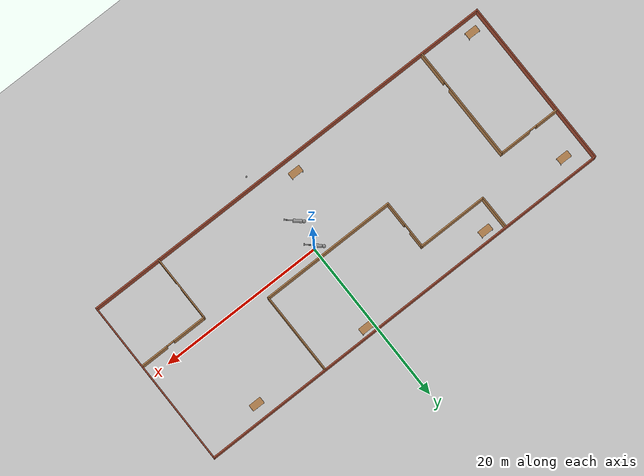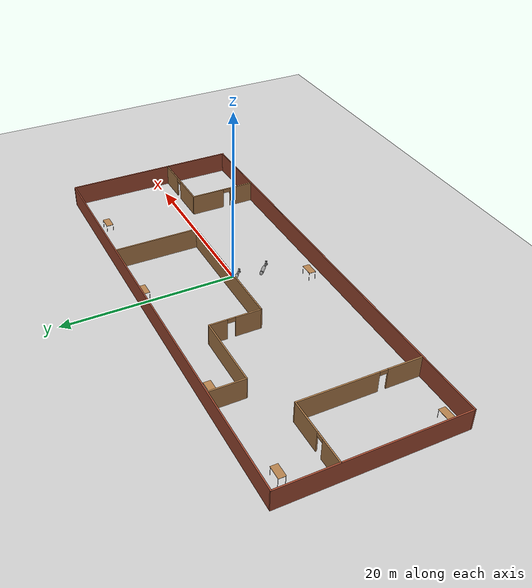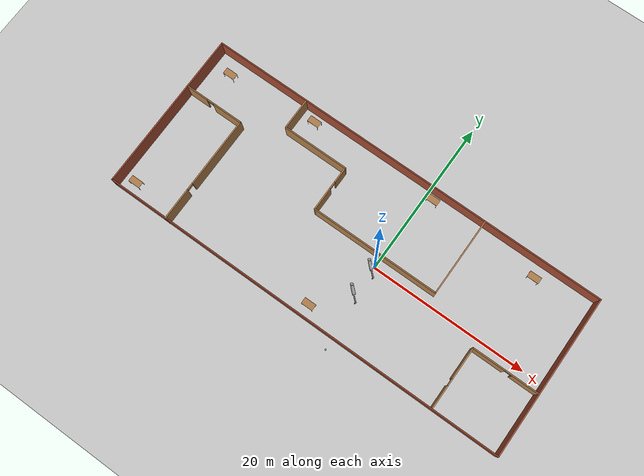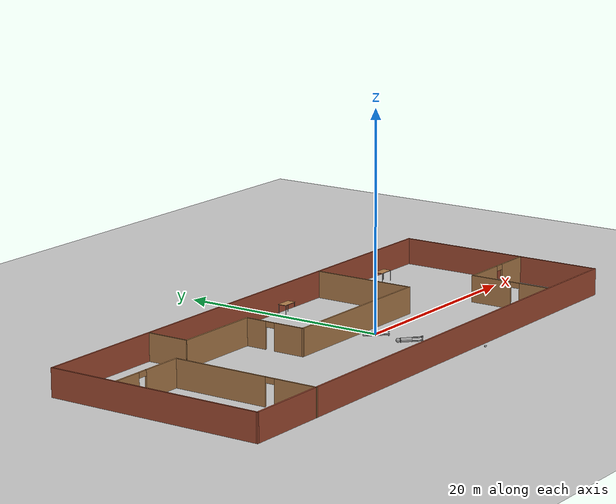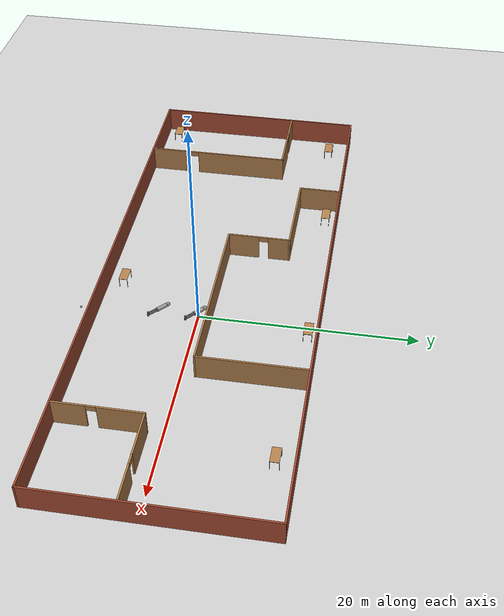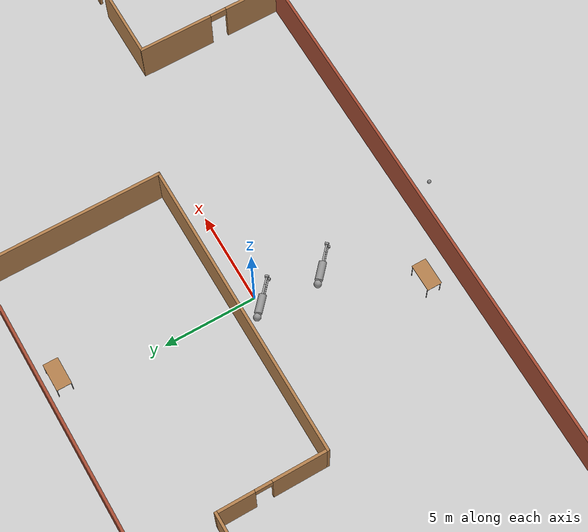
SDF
<sdf version="1.6">
 <world name="default">
  <model name="ground_plane">
   <static>1</static>
   <link name="link">
    <collision name="collision">
     <geometry><plane><normal>0 0 1</normal><size>100 100</size></plane></geometry>
     <surface><friction><ode><mu>100</mu><mu2>50</mu2></ode></friction></surface>
    </collision>
    <visual name="visual">
     <cast_shadows>0</cast_shadows>
     <geometry><plane><normal>0 0 1</normal><size>100 100</size></plane></geometry>
     <material>
      <script><uri>file://media/materials/scripts/gazebo.material</uri><name>Gazebo/Grey</name></script>
     </material>
    </visual>
   </link>
  </model>
  <light name="sun" type="directional">
   <pose>0 0 10 0 -0 0</pose>
   <diffuse>0.8 0.8 0.8 1</diffuse>
   <specular>0.2 0.2 0.2 1</specular>
   <attenuation>
    <range>1000</range>
    <constant>0.9</constant>
    <linear>0.01</linear>
    <quadratic>0.001</quadratic>
   </attenuation>
   <direction>-0.5 0.1 -0.9</direction>
  </light>
  <gravity>0 0 -9.8</gravity>
  <magnetic_field>6e-06 2.3e-05 -4.2e-05</magnetic_field>
  <atmosphere type="adiabatic"/>
  <physics name="default_physics" default="0" type="ode">
   <max_step_size>0.001</max_step_size>
   <real_time_factor>1</real_time_factor>
   <real_time_update_rate>1000</real_time_update_rate>
  </physics>
  <scene><ambient>0.4 0.4 0.4 1</ambient><background>0.7 0.7 0.7 1</background><shadows>1</shadows></scene>
  <spherical_coordinates>
   <surface_model>EARTH_WGS84</surface_model>
   <latitude_deg>0</latitude_deg>
   <longitude_deg>0</longitude_deg>
   <elevation>0</elevation>
   <heading_deg>0</heading_deg>
  </spherical_coordinates>
  <model name="My_building">
   <pose>-3.695 0.89314 0 0 -0 0</pose>
   <link name="Wall_10">
    <collision name="Wall_10_Collision">
     <geometry><box><size>4 0.15 2.5</size></box></geometry>
     <pose>0 0 1.25 0 -0 0</pose>
    </collision>
    <visual name="Wall_10_Visual">
     <pose>0 0 1.25 0 -0 0</pose>
     <geometry><box><size>4 0.15 2.5</size></box></geometry>
     <material>
      <script><uri>file://media/materials/scripts/gazebo.material</uri><name>Gazebo/Wood</name></script>
      <ambient>1 1 1 1</ambient>
     </material>
     <meta><layer>0</layer></meta>
    </visual>
    <pose>-13.7983 8.19008 0 0 -0 1.5708</pose>
   </link>
   <link name="Wall_13">
    <collision name="Wall_13_Collision">
     <geometry><box><size>10 0.15 2.5</size></box></geometry>
     <pose>0 0 1.25 0 -0 0</pose>
    </collision>
    <visual name="Wall_13_Visual">
     <pose>0 0 1.25 0 -0 0</pose>
     <geometry><box><size>10 0.15 2.5</size></box></geometry>
     <material>
      <script><uri>file://media/materials/scripts/gazebo.material</uri><name>Gazebo/Wood</name></script>
      <ambient>1 1 1 1</ambient>
     </material>
     <meta><layer>0</layer></meta>
    </visual>
    <pose>10.9198 5.26327 0 0 0 -1.5708</pose>
   </link>
   <link name="Wall_14">
    <collision name="Wall_14_Collision">
     <geometry><box><size>16.5 0.15 2.5</size></box></geometry>
     <pose>0 0 1.25 0 -0 0</pose>
    </collision>
    <visual name="Wall_14_Visual">
     <pose>0 0 1.25 0 -0 0</pose>
     <geometry><box><size>16.5 0.15 2.5</size></box></geometry>
     <material>
      <script><uri>file://media/materials/scripts/gazebo.material</uri><name>Gazebo/Wood</name></script>
      <ambient>0.996078 0.47451 0.0196078 1</ambient>
     </material>
     <meta><layer>0</layer></meta>
    </visual>
    <pose>2.74482 0.338271 0 0 -0 3.14159</pose>
   </link>
   <link name="Wall_15">
    <pose>-5.43018 3.26327 0 0 -0 1.5708</pose>
    <visual name="Wall_15_Visual_0">
     <pose>-1.49276 0 1.25 0 -0 0</pose>
     <geometry><box><size>3.01449 0.15 2.5</size></box></geometry>
     <material>
      <script><uri>file://media/materials/scripts/gazebo.material</uri><name>Gazebo/Wood</name></script>
      <ambient>1 1 1 1</ambient>
     </material>
     <meta><layer>0</layer></meta>
    </visual>
    <collision name="Wall_15_Collision_0">
     <geometry><box><size>3.01449 0.15 2.5</size></box></geometry>
     <pose>-1.49276 0 1.25 0 -0 0</pose>
    </collision>
    <visual name="Wall_15_Visual_1">
     <pose>1.95724 0 1.25 0 -0 0</pose>
     <geometry><box><size>2.08551 0.15 2.5</size></box></geometry>
     <material>
      <script><uri>file://media/materials/scripts/gazebo.material</uri><name>Gazebo/Wood</name></script>
      <ambient>1 1 1 1</ambient>
     </material>
     <meta><layer>0</layer></meta>
    </visual>
    <collision name="Wall_15_Collision_1">
     <geometry><box><size>2.08551 0.15 2.5</size></box></geometry>
     <pose>1.95724 0 1.25 0 -0 0</pose>
    </collision>
    <visual name="Wall_15_Visual_2">
     <pose>0.464491 0 2.25 0 -0 0</pose>
     <geometry><box><size>0.9 0.15 0.5</size></box></geometry>
     <material>
      <script><uri>file://media/materials/scripts/gazebo.material</uri><name>Gazebo/Wood</name></script>
      <ambient>1 1 1 1</ambient>
     </material>
     <meta><layer>0</layer></meta>
    </visual>
    <collision name="Wall_15_Collision_2">
     <geometry><box><size>0.9 0.15 0.5</size></box></geometry>
     <pose>0.464491 0 2.25 0 -0 0</pose>
    </collision>
   </link>
   <link name="Wall_16">
    <collision name="Wall_16_Collision">
     <geometry><box><size>8.5 0.15 2.5</size></box></geometry>
     <pose>0 0 1.25 0 -0 0</pose>
    </collision>
    <visual name="Wall_16_Visual">
     <pose>0 0 1.25 0 -0 0</pose>
     <geometry><box><size>8.5 0.15 2.5</size></box></geometry>
     <material>
      <script><uri>file://media/materials/scripts/gazebo.material</uri><name>Gazebo/Wood</name></script>
      <ambient>1 1 1 1</ambient>
     </material>
     <meta><layer>0</layer></meta>
    </visual>
    <pose>-9.60518 6.18827 0 0 -0 3.14159</pose>
   </link>
   <link name="Wall_23">
    <pose>17.6076 -6.18169 0 0 -0 1.5708</pose>
    <visual name="Wall_23_Visual_0">
     <pose>-2.48677 0 1.25 0 -0 0</pose>
     <geometry><box><size>3.02646 0.15 2.5</size></box></geometry>
     <material>
      <script><uri>file://media/materials/scripts/gazebo.material</uri><name>Gazebo/Wood</name></script>
      <ambient>1 1 1 1</ambient>
     </material>
     <meta><layer>0</layer></meta>
    </visual>
    <collision name="Wall_23_Collision_0">
     <geometry><box><size>3.02646 0.15 2.5</size></box></geometry>
     <pose>-2.48677 0 1.25 0 -0 0</pose>
    </collision>
    <visual name="Wall_23_Visual_1">
     <pose>1.96323 0 1.25 0 -0 0</pose>
     <geometry><box><size>4.07354 0.15 2.5</size></box></geometry>
     <material>
      <script><uri>file://media/materials/scripts/gazebo.material</uri><name>Gazebo/Wood</name></script>
      <ambient>1 1 1 1</ambient>
     </material>
     <meta><layer>0</layer></meta>
    </visual>
    <collision name="Wall_23_Collision_1">
     <geometry><box><size>4.07354 0.15 2.5</size></box></geometry>
     <pose>1.96323 0 1.25 0 -0 0</pose>
    </collision>
    <visual name="Wall_23_Visual_2">
     <pose>-0.523537 0 2.25 0 -0 0</pose>
     <geometry><box><size>0.9 0.15 0.5</size></box></geometry>
     <material>
      <script><uri>file://media/materials/scripts/gazebo.material</uri><name>Gazebo/Wood</name></script>
      <ambient>1 1 1 1</ambient>
     </material>
     <meta><layer>0</layer></meta>
    </visual>
    <collision name="Wall_23_Collision_2">
     <geometry><box><size>0.9 0.15 0.5</size></box></geometry>
     <pose>-0.523537 0 2.25 0 -0 0</pose>
    </collision>
   </link>
   <link name="Wall_24">
    <pose>21.7826 -2.25669 0 0 -0 0</pose>
    <visual name="Wall_24_Visual_0">
     <pose>-2.14293 0 1.25 0 -0 0</pose>
     <geometry><box><size>4.21413 0.15 2.5</size></box></geometry>
     <material>
      <script><uri>file://media/materials/scripts/gazebo.material</uri><name>Gazebo/Wood</name></script>
      <ambient>1 1 1 1</ambient>
     </material>
     <meta><layer>0</layer></meta>
    </visual>
    <collision name="Wall_24_Collision_0">
     <geometry><box><size>4.21413 0.15 2.5</size></box></geometry>
     <pose>-2.14293 0 1.25 0 -0 0</pose>
    </collision>
    <visual name="Wall_24_Visual_1">
     <pose>2.55707 0 1.25 0 -0 0</pose>
     <geometry><box><size>3.38587 0.15 2.5</size></box></geometry>
     <material>
      <script><uri>file://media/materials/scripts/gazebo.material</uri><name>Gazebo/Wood</name></script>
      <ambient>1 1 1 1</ambient>
     </material>
     <meta><layer>0</layer></meta>
    </visual>
    <collision name="Wall_24_Collision_1">
     <geometry><box><size>3.38587 0.15 2.5</size></box></geometry>
     <pose>2.55707 0 1.25 0 -0 0</pose>
    </collision>
    <visual name="Wall_24_Visual_2">
     <pose>0.414131 0 2.25 0 -0 0</pose>
     <geometry><box><size>0.9 0.15 0.5</size></box></geometry>
     <material>
      <script><uri>file://media/materials/scripts/gazebo.material</uri><name>Gazebo/Wood</name></script>
      <ambient>1 1 1 1</ambient>
     </material>
     <meta><layer>0</layer></meta>
    </visual>
    <collision name="Wall_24_Collision_2">
     <geometry><box><size>0.9 0.15 0.5</size></box></geometry>
     <pose>0.414131 0 2.25 0 -0 0</pose>
    </collision>
   </link>
   <link name="Wall_26">
    <pose>-22.1969 3.66097 0 0 -0 0</pose>
    <visual name="Wall_26_Visual_0">
     <pose>-2.43672 0 1.25 0 -0 0</pose>
     <geometry><box><size>2.87657 0.15 2.5</size></box></geometry>
     <material>
      <script><uri>file://media/materials/scripts/gazebo.material</uri><name>Gazebo/Wood</name></script>
      <ambient>1 1 1 1</ambient>
     </material>
     <meta><layer>0</layer></meta>
    </visual>
    <collision name="Wall_26_Collision_0">
     <geometry><box><size>2.87657 0.15 2.5</size></box></geometry>
     <pose>-2.43672 0 1.25 0 -0 0</pose>
    </collision>
    <visual name="Wall_26_Visual_1">
     <pose>1.88828 0 1.25 0 -0 0</pose>
     <geometry><box><size>3.97343 0.15 2.5</size></box></geometry>
     <material>
      <script><uri>file://media/materials/scripts/gazebo.material</uri><name>Gazebo/Wood</name></script>
      <ambient>1 1 1 1</ambient>
     </material>
     <meta><layer>0</layer></meta>
    </visual>
    <collision name="Wall_26_Collision_1">
     <geometry><box><size>3.97343 0.15 2.5</size></box></geometry>
     <pose>1.88828 0 1.25 0 -0 0</pose>
    </collision>
    <visual name="Wall_26_Visual_2">
     <pose>-0.548431 0 2.25 0 -0 0</pose>
     <geometry><box><size>0.9 0.15 0.5</size></box></geometry>
     <material>
      <script><uri>file://media/materials/scripts/gazebo.material</uri><name>Gazebo/Wood</name></script>
      <ambient>1 1 1 1</ambient>
     </material>
     <meta><layer>0</layer></meta>
    </visual>
    <collision name="Wall_26_Collision_2">
     <geometry><box><size>0.9 0.15 0.5</size></box></geometry>
     <pose>-0.548431 0 2.25 0 -0 0</pose>
    </collision>
   </link>
   <link name="Wall_27">
    <pose>-18.3969 -3.26403 0 0 0 -1.5708</pose>
    <visual name="Wall_27_Visual_0">
     <pose>-2.48593 0 1.25 0 -0 0</pose>
     <geometry><box><size>9.02815 0.15 2.5</size></box></geometry>
     <material>
      <script><uri>file://media/materials/scripts/gazebo.material</uri><name>Gazebo/Wood</name></script>
      <ambient>0.996078 0.47451 0.0196078 1</ambient>
     </material>
     <meta><layer>0</layer></meta>
    </visual>
    <collision name="Wall_27_Collision_0">
     <geometry><box><size>9.02815 0.15 2.5</size></box></geometry>
     <pose>-2.48593 0 1.25 0 -0 0</pose>
    </collision>
    <visual name="Wall_27_Visual_1">
     <pose>4.96407 0 1.25 0 -0 0</pose>
     <geometry><box><size>4.07185 0.15 2.5</size></box></geometry>
     <material>
      <script><uri>file://media/materials/scripts/gazebo.material</uri><name>Gazebo/Wood</name></script>
      <ambient>0.996078 0.47451 0.0196078 1</ambient>
     </material>
     <meta><layer>0</layer></meta>
    </visual>
    <collision name="Wall_27_Collision_1">
     <geometry><box><size>4.07185 0.15 2.5</size></box></geometry>
     <pose>4.96407 0 1.25 0 -0 0</pose>
    </collision>
    <visual name="Wall_27_Visual_2">
     <pose>2.47815 0 2.25 0 -0 0</pose>
     <geometry><box><size>0.9 0.15 0.5</size></box></geometry>
     <material>
      <script><uri>file://media/materials/scripts/gazebo.material</uri><name>Gazebo/Wood</name></script>
      <ambient>0.996078 0.47451 0.0196078 1</ambient>
     </material>
     <meta><layer>0</layer></meta>
    </visual>
    <collision name="Wall_27_Collision_2">
     <geometry><box><size>0.9 0.15 0.5</size></box></geometry>
     <pose>2.47815 0 2.25 0 -0 0</pose>
    </collision>
   </link>
   <link name="Wall_3">
    <collision name="Wall_3_Collision">
     <geometry><box><size>52.25 0.15 2.5</size></box></geometry>
     <pose>0 0 1.25 0 -0 0</pose>
    </collision>
    <visual name="Wall_3_Visual">
     <pose>0 0 1.25 0 -0 0</pose>
     <geometry><box><size>52.25 0.15 2.5</size></box></geometry>
     <material>
      <script><uri>file://media/materials/scripts/gazebo.material</uri><name>Gazebo/Bricks</name></script>
      <ambient>1 1 1 1</ambient>
     </material>
     <meta><layer>0</layer></meta>
    </visual>
    <pose>-1e-06 10.189 0 0 -0 0</pose>
   </link>
   <link name="Wall_4">
    <collision name="Wall_4_Collision">
     <geometry><box><size>20.5 0.15 2.5</size></box></geometry>
     <pose>0 0 1.25 0 -0 0</pose>
    </collision>
    <visual name="Wall_4_Visual">
     <pose>0 0 1.25 0 -0 0</pose>
     <geometry><box><size>20.5 0.15 2.5</size></box></geometry>
     <material>
      <script><uri>file://media/materials/scripts/gazebo.material</uri><name>Gazebo/Bricks</name></script>
      <ambient>1 1 1 1</ambient>
     </material>
     <meta><layer>0</layer></meta>
    </visual>
    <pose>26.05 0.014033 0 0 0 -1.5708</pose>
   </link>
   <link name="Wall_5">
    <collision name="Wall_5_Collision">
     <geometry><box><size>52.25 0.15 2.5</size></box></geometry>
     <pose>0 0 1.25 0 -0 0</pose>
    </collision>
    <visual name="Wall_5_Visual">
     <pose>0 0 1.25 0 -0 0</pose>
     <geometry><box><size>52.25 0.15 2.5</size></box></geometry>
     <material>
      <script><uri>file://media/materials/scripts/gazebo.material</uri><name>Gazebo/Bricks</name></script>
      <ambient>1 1 1 1</ambient>
     </material>
     <meta><layer>0</layer></meta>
    </visual>
    <pose>-1e-06 -10.161 0 0 -0 3.14159</pose>
   </link>
   <link name="Wall_6">
    <collision name="Wall_6_Collision">
     <geometry><box><size>20.5 0.15 2.5</size></box></geometry>
     <pose>0 0 1.25 0 -0 0</pose>
    </collision>
    <visual name="Wall_6_Visual">
     <pose>0 0 1.25 0 -0 0</pose>
     <geometry><box><size>20.5 0.15 2.5</size></box></geometry>
     <material>
      <script><uri>file://media/materials/scripts/gazebo.material</uri><name>Gazebo/Bricks</name></script>
      <ambient>1 1 1 1</ambient>
     </material>
     <meta><layer>0</layer></meta>
    </visual>
    <pose>-26.05 0.014033 0 0 -0 1.5708</pose>
   </link>
   <static>1</static>
  </model>
  <model name="table">
   <static>1</static>
   <link name="link">
    <collision name="surface">
     <pose>0 0 1 0 -0 0</pose>
     <geometry><box><size>1.5 0.8 0.03</size></box></geometry>
     <surface><friction><ode><mu>0.6</mu><mu2>0.6</mu2></ode></friction></surface>
    </collision>
    <visual name="visual1">
     <pose>0 0 1 0 -0 0</pose>
     <geometry><box><size>1.5 0.8 0.03</size></box></geometry>
     <material>
      <script><uri>file://media/materials/scripts/gazebo.material</uri><name>Gazebo/Wood</name></script>
     </material>
    </visual>
    <collision name="front_left_leg">
     <pose>0.68 0.38 0.5 0 -0 0</pose>
     <geometry><cylinder><radius>0.02</radius><length>1</length></cylinder></geometry>
    </collision>
    <visual name="front_left_leg">
     <pose>0.68 0.38 0.5 0 -0 0</pose>
     <geometry><cylinder><radius>0.02</radius><length>1</length></cylinder></geometry>
     <material>
      <script><uri>file://media/materials/scripts/gazebo.material</uri><name>Gazebo/Grey</name></script>
     </material>
    </visual>
    <collision name="front_right_leg">
     <pose>0.68 -0.38 0.5 0 -0 0</pose>
     <geometry><cylinder><radius>0.02</radius><length>1</length></cylinder></geometry>
    </collision>
    <visual name="front_right_leg">
     <pose>0.68 -0.38 0.5 0 -0 0</pose>
     <geometry><cylinder><radius>0.02</radius><length>1</length></cylinder></geometry>
     <material>
      <script><uri>file://media/materials/scripts/gazebo.material</uri><name>Gazebo/Grey</name></script>
     </material>
    </visual>
    <collision name="back_right_leg">
     <pose>-0.68 -0.38 0.5 0 -0 0</pose>
     <geometry><cylinder><radius>0.02</radius><length>1</length></cylinder></geometry>
    </collision>
    <visual name="back_right_leg">
     <pose>-0.68 -0.38 0.5 0 -0 0</pose>
     <geometry><cylinder><radius>0.02</radius><length>1</length></cylinder></geometry>
     <material>
      <script><uri>file://media/materials/scripts/gazebo.material</uri><name>Gazebo/Grey</name></script>
     </material>
    </visual>
    <collision name="back_left_leg">
     <pose>-0.68 0.38 0.5 0 -0 0</pose>
     <geometry><cylinder><radius>0.02</radius><length>1</length></cylinder></geometry>
    </collision>
    <visual name="back_left_leg">
     <pose>-0.68 0.38 0.5 0 -0 0</pose>
     <geometry><cylinder><radius>0.02</radius><length>1</length></cylinder></geometry>
     <material>
      <script><uri>file://media/materials/scripts/gazebo.material</uri><name>Gazebo/Grey</name></script>
     </material>
    </visual>
   </link>
   <pose>-3.54039 -7.70707 0 0 -0 0</pose>
  </model>
  <model name="table_0">
   <static>1</static>
   <link name="link">
    <collision name="surface">
     <pose>0 0 1 0 -0 0</pose>
     <geometry><box><size>1.5 0.8 0.03</size></box></geometry>
     <surface><friction><ode><mu>0.6</mu><mu2>0.6</mu2></ode></friction></surface>
    </collision>
    <visual name="visual1">
     <pose>0 0 1 0 -0 0</pose>
     <geometry><box><size>1.5 0.8 0.03</size></box></geometry>
     <material>
      <script><uri>file://media/materials/scripts/gazebo.material</uri><name>Gazebo/Wood</name></script>
     </material>
    </visual>
    <collision name="front_left_leg">
     <pose>0.68 0.38 0.5 0 -0 0</pose>
     <geometry><cylinder><radius>0.02</radius><length>1</length></cylinder></geometry>
    </collision>
    <visual name="front_left_leg">
     <pose>0.68 0.38 0.5 0 -0 0</pose>
     <geometry><cylinder><radius>0.02</radius><length>1</length></cylinder></geometry>
     <material>
      <script><uri>file://media/materials/scripts/gazebo.material</uri><name>Gazebo/Grey</name></script>
     </material>
    </visual>
    <collision name="front_right_leg">
     <pose>0.68 -0.38 0.5 0 -0 0</pose>
     <geometry><cylinder><radius>0.02</radius><length>1</length></cylinder></geometry>
    </collision>
    <visual name="front_right_leg">
     <pose>0.68 -0.38 0.5 0 -0 0</pose>
     <geometry><cylinder><radius>0.02</radius><length>1</length></cylinder></geometry>
     <material>
      <script><uri>file://media/materials/scripts/gazebo.material</uri><name>Gazebo/Grey</name></script>
     </material>
    </visual>
    <collision name="back_right_leg">
     <pose>-0.68 -0.38 0.5 0 -0 0</pose>
     <geometry><cylinder><radius>0.02</radius><length>1</length></cylinder></geometry>
    </collision>
    <visual name="back_right_leg">
     <pose>-0.68 -0.38 0.5 0 -0 0</pose>
     <geometry><cylinder><radius>0.02</radius><length>1</length></cylinder></geometry>
     <material>
      <script><uri>file://media/materials/scripts/gazebo.material</uri><name>Gazebo/Grey</name></script>
     </material>
    </visual>
    <collision name="back_left_leg">
     <pose>-0.68 0.38 0.5 0 -0 0</pose>
     <geometry><cylinder><radius>0.02</radius><length>1</length></cylinder></geometry>
    </collision>
    <visual name="back_left_leg">
     <pose>-0.68 0.38 0.5 0 -0 0</pose>
     <geometry><cylinder><radius>0.02</radius><length>1</length></cylinder></geometry>
     <material>
      <script><uri>file://media/materials/scripts/gazebo.material</uri><name>Gazebo/Grey</name></script>
     </material>
    </visual>
   </link>
   <pose>0.966059 10.1952 0 0 -0 0</pose>
  </model>
  <model name="table_1">
   <static>1</static>
   <link name="link">
    <collision name="surface">
     <pose>0 0 1 0 -0 0</pose>
     <geometry><box><size>1.5 0.8 0.03</size></box></geometry>
     <surface><friction><ode><mu>0.6</mu><mu2>0.6</mu2></ode></friction></surface>
    </collision>
    <visual name="visual1">
     <pose>0 0 1 0 -0 0</pose>
     <geometry><box><size>1.5 0.8 0.03</size></box></geometry>
     <material>
      <script><uri>file://media/materials/scripts/gazebo.material</uri><name>Gazebo/Wood</name></script>
     </material>
    </visual>
    <collision name="front_left_leg">
     <pose>0.68 0.38 0.5 0 -0 0</pose>
     <geometry><cylinder><radius>0.02</radius><length>1</length></cylinder></geometry>
    </collision>
    <visual name="front_left_leg">
     <pose>0.68 0.38 0.5 0 -0 0</pose>
     <geometry><cylinder><radius>0.02</radius><length>1</length></cylinder></geometry>
     <material>
      <script><uri>file://media/materials/scripts/gazebo.material</uri><name>Gazebo/Grey</name></script>
     </material>
    </visual>
    <collision name="front_right_leg">
     <pose>0.68 -0.38 0.5 0 -0 0</pose>
     <geometry><cylinder><radius>0.02</radius><length>1</length></cylinder></geometry>
    </collision>
    <visual name="front_right_leg">
     <pose>0.68 -0.38 0.5 0 -0 0</pose>
     <geometry><cylinder><radius>0.02</radius><length>1</length></cylinder></geometry>
     <material>
      <script><uri>file://media/materials/scripts/gazebo.material</uri><name>Gazebo/Grey</name></script>
     </material>
    </visual>
    <collision name="back_right_leg">
     <pose>-0.68 -0.38 0.5 0 -0 0</pose>
     <geometry><cylinder><radius>0.02</radius><length>1</length></cylinder></geometry>
    </collision>
    <visual name="back_right_leg">
     <pose>-0.68 -0.38 0.5 0 -0 0</pose>
     <geometry><cylinder><radius>0.02</radius><length>1</length></cylinder></geometry>
     <material>
      <script><uri>file://media/materials/scripts/gazebo.material</uri><name>Gazebo/Grey</name></script>
     </material>
    </visual>
    <collision name="back_left_leg">
     <pose>-0.68 0.38 0.5 0 -0 0</pose>
     <geometry><cylinder><radius>0.02</radius><length>1</length></cylinder></geometry>
    </collision>
    <visual name="back_left_leg">
     <pose>-0.68 0.38 0.5 0 -0 0</pose>
     <geometry><cylinder><radius>0.02</radius><length>1</length></cylinder></geometry>
     <material>
      <script><uri>file://media/materials/scripts/gazebo.material</uri><name>Gazebo/Grey</name></script>
     </material>
    </visual>
   </link>
   <pose>-15.6009 9.94625 0 0 -0 0</pose>
  </model>
  <model name="table_2">
   <static>1</static>
   <link name="link">
    <collision name="surface">
     <pose>0 0 1 0 -0 0</pose>
     <geometry><box><size>1.5 0.8 0.03</size></box></geometry>
     <surface><friction><ode><mu>0.6</mu><mu2>0.6</mu2></ode></friction></surface>
    </collision>
    <visual name="visual1">
     <pose>0 0 1 0 -0 0</pose>
     <geometry><box><size>1.5 0.8 0.03</size></box></geometry>
     <material>
      <script><uri>file://media/materials/scripts/gazebo.material</uri><name>Gazebo/Wood</name></script>
     </material>
    </visual>
    <collision name="front_left_leg">
     <pose>0.68 0.38 0.5 0 -0 0</pose>
     <geometry><cylinder><radius>0.02</radius><length>1</length></cylinder></geometry>
    </collision>
    <visual name="front_left_leg">
     <pose>0.68 0.38 0.5 0 -0 0</pose>
     <geometry><cylinder><radius>0.02</radius><length>1</length></cylinder></geometry>
     <material>
      <script><uri>file://media/materials/scripts/gazebo.material</uri><name>Gazebo/Grey</name></script>
     </material>
    </visual>
    <collision name="front_right_leg">
     <pose>0.68 -0.38 0.5 0 -0 0</pose>
     <geometry><cylinder><radius>0.02</radius><length>1</length></cylinder></geometry>
    </collision>
    <visual name="front_right_leg">
     <pose>0.68 -0.38 0.5 0 -0 0</pose>
     <geometry><cylinder><radius>0.02</radius><length>1</length></cylinder></geometry>
     <material>
      <script><uri>file://media/materials/scripts/gazebo.material</uri><name>Gazebo/Grey</name></script>
     </material>
    </visual>
    <collision name="back_right_leg">
     <pose>-0.68 -0.38 0.5 0 -0 0</pose>
     <geometry><cylinder><radius>0.02</radius><length>1</length></cylinder></geometry>
    </collision>
    <visual name="back_right_leg">
     <pose>-0.68 -0.38 0.5 0 -0 0</pose>
     <geometry><cylinder><radius>0.02</radius><length>1</length></cylinder></geometry>
     <material>
      <script><uri>file://media/materials/scripts/gazebo.material</uri><name>Gazebo/Grey</name></script>
     </material>
    </visual>
    <collision name="back_left_leg">
     <pose>-0.68 0.38 0.5 0 -0 0</pose>
     <geometry><cylinder><radius>0.02</radius><length>1</length></cylinder></geometry>
    </collision>
    <visual name="back_left_leg">
     <pose>-0.68 0.38 0.5 0 -0 0</pose>
     <geometry><cylinder><radius>0.02</radius><length>1</length></cylinder></geometry>
     <material>
      <script><uri>file://media/materials/scripts/gazebo.material</uri><name>Gazebo/Grey</name></script>
     </material>
    </visual>
   </link>
   <pose>15.2329 9.3558 0 0 -0 0</pose>
  </model>
  <model name="table_3">
   <static>1</static>
   <link name="link">
    <collision name="surface">
     <pose>0 0 1 0 -0 0</pose>
     <geometry><box><size>1.5 0.8 0.03</size></box></geometry>
     <surface><friction><ode><mu>0.6</mu><mu2>0.6</mu2></ode></friction></surface>
    </collision>
    <visual name="visual1">
     <pose>0 0 1 0 -0 0</pose>
     <geometry><box><size>1.5 0.8 0.03</size></box></geometry>
     <material>
      <script><uri>file://media/materials/scripts/gazebo.material</uri><name>Gazebo/Wood</name></script>
     </material>
    </visual>
    <collision name="front_left_leg">
     <pose>0.68 0.38 0.5 0 -0 0</pose>
     <geometry><cylinder><radius>0.02</radius><length>1</length></cylinder></geometry>
    </collision>
    <visual name="front_left_leg">
     <pose>0.68 0.38 0.5 0 -0 0</pose>
     <geometry><cylinder><radius>0.02</radius><length>1</length></cylinder></geometry>
     <material>
      <script><uri>file://media/materials/scripts/gazebo.material</uri><name>Gazebo/Grey</name></script>
     </material>
    </visual>
    <collision name="front_right_leg">
     <pose>0.68 -0.38 0.5 0 -0 0</pose>
     <geometry><cylinder><radius>0.02</radius><length>1</length></cylinder></geometry>
    </collision>
    <visual name="front_right_leg">
     <pose>0.68 -0.38 0.5 0 -0 0</pose>
     <geometry><cylinder><radius>0.02</radius><length>1</length></cylinder></geometry>
     <material>
      <script><uri>file://media/materials/scripts/gazebo.material</uri><name>Gazebo/Grey</name></script>
     </material>
    </visual>
    <collision name="back_right_leg">
     <pose>-0.68 -0.38 0.5 0 -0 0</pose>
     <geometry><cylinder><radius>0.02</radius><length>1</length></cylinder></geometry>
    </collision>
    <visual name="back_right_leg">
     <pose>-0.68 -0.38 0.5 0 -0 0</pose>
     <geometry><cylinder><radius>0.02</radius><length>1</length></cylinder></geometry>
     <material>
      <script><uri>file://media/materials/scripts/gazebo.material</uri><name>Gazebo/Grey</name></script>
     </material>
    </visual>
    <collision name="back_left_leg">
     <pose>-0.68 0.38 0.5 0 -0 0</pose>
     <geometry><cylinder><radius>0.02</radius><length>1</length></cylinder></geometry>
    </collision>
    <visual name="back_left_leg">
     <pose>-0.68 0.38 0.5 0 -0 0</pose>
     <geometry><cylinder><radius>0.02</radius><length>1</length></cylinder></geometry>
     <material>
      <script><uri>file://media/materials/scripts/gazebo.material</uri><name>Gazebo/Grey</name></script>
     </material>
    </visual>
   </link>
   <pose>-27.2072 9.00097 0 0 -0 0</pose>
  </model>
  <model name="table_4">
   <static>1</static>
   <link name="link">
    <collision name="surface">
     <pose>0 0 1 0 -0 0</pose>
     <geometry><box><size>1.5 0.8 0.03</size></box></geometry>
     <surface><friction><ode><mu>0.6</mu><mu2>0.6</mu2></ode></friction></surface>
    </collision>
    <visual name="visual1">
     <pose>0 0 1 0 -0 0</pose>
     <geometry><box><size>1.5 0.8 0.03</size></box></geometry>
     <material>
      <script><uri>file://media/materials/scripts/gazebo.material</uri><name>Gazebo/Wood</name></script>
     </material>
    </visual>
    <collision name="front_left_leg">
     <pose>0.68 0.38 0.5 0 -0 0</pose>
     <geometry><cylinder><radius>0.02</radius><length>1</length></cylinder></geometry>
    </collision>
    <visual name="front_left_leg">
     <pose>0.68 0.38 0.5 0 -0 0</pose>
     <geometry><cylinder><radius>0.02</radius><length>1</length></cylinder></geometry>
     <material>
      <script><uri>file://media/materials/scripts/gazebo.material</uri><name>Gazebo/Grey</name></script>
     </material>
    </visual>
    <collision name="front_right_leg">
     <pose>0.68 -0.38 0.5 0 -0 0</pose>
     <geometry><cylinder><radius>0.02</radius><length>1</length></cylinder></geometry>
    </collision>
    <visual name="front_right_leg">
     <pose>0.68 -0.38 0.5 0 -0 0</pose>
     <geometry><cylinder><radius>0.02</radius><length>1</length></cylinder></geometry>
     <material>
      <script><uri>file://media/materials/scripts/gazebo.material</uri><name>Gazebo/Grey</name></script>
     </material>
    </visual>
    <collision name="back_right_leg">
     <pose>-0.68 -0.38 0.5 0 -0 0</pose>
     <geometry><cylinder><radius>0.02</radius><length>1</length></cylinder></geometry>
    </collision>
    <visual name="back_right_leg">
     <pose>-0.68 -0.38 0.5 0 -0 0</pose>
     <geometry><cylinder><radius>0.02</radius><length>1</length></cylinder></geometry>
     <material>
      <script><uri>file://media/materials/scripts/gazebo.material</uri><name>Gazebo/Grey</name></script>
     </material>
    </visual>
    <collision name="back_left_leg">
     <pose>-0.68 0.38 0.5 0 -0 0</pose>
     <geometry><cylinder><radius>0.02</radius><length>1</length></cylinder></geometry>
    </collision>
    <visual name="back_left_leg">
     <pose>-0.68 0.38 0.5 0 -0 0</pose>
     <geometry><cylinder><radius>0.02</radius><length>1</length></cylinder></geometry>
     <material>
      <script><uri>file://media/materials/scripts/gazebo.material</uri><name>Gazebo/Grey</name></script>
     </material>
    </visual>
   </link>
   <pose>-28.0015 -7.81856 0 0 -0 0</pose>
  </model>
  <model name="humanoid_1">
   <link name="link_0">
    <pose>0.0025 0.019375 0.775 0 -0 0</pose>
    <inertial>
     <mass>1</mass>
     <inertia><ixx>0.145833</ixx><ixy>0</ixy><ixz>0</ixz><iyy>0.145833</iyy><iyz>0</iyz><izz>0.125</izz></inertia>
    </inertial>
    <visual name="visual">
     <geometry><cylinder><radius>0.2</radius><length>1</length></cylinder></geometry>
     <material>
      <lighting>1</lighting>
      <script><uri>file://media/materials/scripts/gazebo.material</uri><name>Gazebo/Grey</name></script>
      <shader type="pixel"><normal_map>__default__</normal_map></shader>
      <ambient>0.3 0.3 0.3 1</ambient>
      <diffuse>0.7 0.7 0.7 1</diffuse>
      <specular>0.01 0.01 0.01 1</specular>
      <emissive>0 0 0 1</emissive>
     </material>
    </visual>
    <collision name="collision">
     <geometry><cylinder><radius>0.2</radius><length>1</length></cylinder></geometry>
     <surface>
      <friction>
       <ode><mu>1</mu><mu2>1</mu2><fdir1>0 0 0</fdir1><slip1>0</slip1><slip2>0</slip2></ode>
       <torsional>
        <coefficient>1</coefficient>
        <patch_radius>0</patch_radius>
        <surface_radius>0</surface_radius>
        <use_patch_radius>1</use_patch_radius>
        <ode><slip>0</slip></ode>
       </torsional>
      </friction>
      <bounce><restitution_coefficient>0</restitution_coefficient><threshold>1e+06</threshold></bounce>
      <contact>
       <collide_without_contact>0</collide_without_contact>
       <collide_without_contact_bitmask>1</collide_without_contact_bitmask>
       <collide_bitmask>1</collide_bitmask>
       <ode>
        <soft_cfm>0</soft_cfm>
        <soft_erp>0.2</soft_erp>
        <kp>1e+13</kp>
        <kd>1</kd>
        <max_vel>0.01</max_vel>
        <min_depth>0</min_depth>
       </ode>
       <bullet>
        <split_impulse>1</split_impulse>
        <split_impulse_penetration_threshold>-0.01</split_impulse_penetration_threshold>
        <soft_cfm>0</soft_cfm>
        <soft_erp>0.2</soft_erp>
        <kp>1e+13</kp>
        <kd>1</kd>
       </bullet>
      </contact>
     </surface>
    </collision>
   </link>
   <link name="link_2">
    <pose>0.0025 0.019375 1.475 0 -0 0</pose>
    <inertial>
     <mass>1</mass>
     <inertia><ixx>0.1</ixx><ixy>0</ixy><ixz>0</ixz><iyy>0.1</iyy><iyz>0</iyz><izz>0.1</izz></inertia>
    </inertial>
    <visual name="visual">
     <geometry><sphere><radius>0.2</radius></sphere></geometry>
     <material>
      <lighting>1</lighting>
      <script><uri>file://media/materials/scripts/gazebo.material</uri><name>Gazebo/Grey</name></script>
      <shader type="pixel"><normal_map>__default__</normal_map></shader>
      <ambient>0.3 0.3 0.3 1</ambient>
      <diffuse>0.7 0.7 0.7 1</diffuse>
      <specular>0.01 0.01 0.01 1</specular>
      <emissive>0 0 0 1</emissive>
     </material>
    </visual>
    <collision name="collision">
     <geometry><sphere><radius>0.2</radius></sphere></geometry>
     <surface>
      <friction>
       <ode><mu>1</mu><mu2>1</mu2><fdir1>0 0 0</fdir1><slip1>0</slip1><slip2>0</slip2></ode>
       <torsional>
        <coefficient>1</coefficient>
        <patch_radius>0</patch_radius>
        <surface_radius>0</surface_radius>
        <use_patch_radius>1</use_patch_radius>
        <ode><slip>0</slip></ode>
       </torsional>
      </friction>
      <bounce><restitution_coefficient>0</restitution_coefficient><threshold>1e+06</threshold></bounce>
      <contact>
       <collide_without_contact>0</collide_without_contact>
       <collide_without_contact_bitmask>1</collide_without_contact_bitmask>
       <collide_bitmask>1</collide_bitmask>
       <ode>
        <soft_cfm>0</soft_cfm>
        <soft_erp>0.2</soft_erp>
        <kp>1e+13</kp>
        <kd>1</kd>
        <max_vel>0.01</max_vel>
        <min_depth>0</min_depth>
       </ode>
       <bullet>
        <split_impulse>1</split_impulse>
        <split_impulse_penetration_threshold>-0.01</split_impulse_penetration_threshold>
        <soft_cfm>0</soft_cfm>
        <soft_erp>0.2</soft_erp>
        <kp>1e+13</kp>
        <kd>1</kd>
       </bullet>
      </contact>
     </surface>
    </collision>
   </link>
   <link name="link_4">
    <pose>-0.1475 -0.025625 0.025 0 -0 0</pose>
    <inertial>
     <mass>1</mass>
     <inertia>
      <ixx>0.166667</ixx>
      <ixy>0</ixy>
      <ixz>0</ixz>
      <iyy>0.166667</iyy>
      <iyz>0</iyz>
      <izz>0.166667</izz>
     </inertia>
    </inertial>
    <visual name="visual">
     <geometry><box><size>0.1 0.1 0.5</size></box></geometry>
     <material>
      <lighting>1</lighting>
      <script><uri>file://media/materials/scripts/gazebo.material</uri><name>Gazebo/Grey</name></script>
      <shader type="pixel"><normal_map>__default__</normal_map></shader>
      <ambient>0.3 0.3 0.3 1</ambient>
      <diffuse>0.7 0.7 0.7 1</diffuse>
      <specular>0.01 0.01 0.01 1</specular>
      <emissive>0 0 0 1</emissive>
     </material>
    </visual>
    <collision name="collision">
     <geometry><box><size>0.1 0.1 0.5</size></box></geometry>
     <surface>
      <friction>
       <ode><mu>1</mu><mu2>1</mu2><fdir1>0 0 0</fdir1><slip1>0</slip1><slip2>0</slip2></ode>
       <torsional>
        <coefficient>1</coefficient>
        <patch_radius>0</patch_radius>
        <surface_radius>0</surface_radius>
        <use_patch_radius>1</use_patch_radius>
        <ode><slip>0</slip></ode>
       </torsional>
      </friction>
      <bounce><restitution_coefficient>0</restitution_coefficient><threshold>1e+06</threshold></bounce>
      <contact>
       <collide_without_contact>0</collide_without_contact>
       <collide_without_contact_bitmask>1</collide_without_contact_bitmask>
       <collide_bitmask>1</collide_bitmask>
       <ode>
        <soft_cfm>0</soft_cfm>
        <soft_erp>0.2</soft_erp>
        <kp>1e+13</kp>
        <kd>1</kd>
        <max_vel>0.01</max_vel>
        <min_depth>0</min_depth>
       </ode>
       <bullet>
        <split_impulse>1</split_impulse>
        <split_impulse_penetration_threshold>-0.01</split_impulse_penetration_threshold>
        <soft_cfm>0</soft_cfm>
        <soft_erp>0.2</soft_erp>
        <kp>1e+13</kp>
        <kd>1</kd>
       </bullet>
      </contact>
     </surface>
    </collision>
   </link>
   <link name="link_4_clone">
    <pose>-0.1475 -0.025625 -0.475 0 -0 0</pose>
    <inertial>
     <mass>1</mass>
     <inertia>
      <ixx>0.166667</ixx>
      <ixy>0</ixy>
      <ixz>0</ixz>
      <iyy>0.166667</iyy>
      <iyz>0</iyz>
      <izz>0.166667</izz>
     </inertia>
    </inertial>
    <visual name="visual">
     <geometry><box><size>0.1 0.1 0.5</size></box></geometry>
     <material>
      <lighting>1</lighting>
      <script><uri>file://media/materials/scripts/gazebo.material</uri><name>Gazebo/Grey</name></script>
      <shader type="pixel"><normal_map>__default__</normal_map></shader>
      <ambient>0.3 0.3 0.3 1</ambient>
      <diffuse>0.7 0.7 0.7 1</diffuse>
      <specular>0.01 0.01 0.01 1</specular>
      <emissive>0 0 0 1</emissive>
     </material>
    </visual>
    <collision name="collision">
     <geometry><box><size>0.1 0.1 0.5</size></box></geometry>
     <surface>
      <friction>
       <ode><mu>1</mu><mu2>1</mu2><fdir1>0 0 0</fdir1><slip1>0</slip1><slip2>0</slip2></ode>
       <torsional>
        <coefficient>1</coefficient>
        <patch_radius>0</patch_radius>
        <surface_radius>0</surface_radius>
        <use_patch_radius>1</use_patch_radius>
        <ode><slip>0</slip></ode>
       </torsional>
      </friction>
      <bounce><restitution_coefficient>0</restitution_coefficient><threshold>1e+06</threshold></bounce>
      <contact>
       <collide_without_contact>0</collide_without_contact>
       <collide_without_contact_bitmask>1</collide_without_contact_bitmask>
       <collide_bitmask>1</collide_bitmask>
       <ode>
        <soft_cfm>0</soft_cfm>
        <soft_erp>0.2</soft_erp>
        <kp>1e+13</kp>
        <kd>1</kd>
        <max_vel>0.01</max_vel>
        <min_depth>0</min_depth>
       </ode>
       <bullet>
        <split_impulse>1</split_impulse>
        <split_impulse_penetration_threshold>-0.01</split_impulse_penetration_threshold>
        <soft_cfm>0</soft_cfm>
        <soft_erp>0.2</soft_erp>
        <kp>1e+13</kp>
        <kd>1</kd>
       </bullet>
      </contact>
     </surface>
    </collision>
   </link>
   <link name="link_4_clone_0">
    <pose>0.1525 0.019375 0.025 0 -0 0</pose>
    <inertial>
     <mass>1</mass>
     <inertia>
      <ixx>0.166667</ixx>
      <ixy>0</ixy>
      <ixz>0</ixz>
      <iyy>0.166667</iyy>
      <iyz>0</iyz>
      <izz>0.166667</izz>
     </inertia>
    </inertial>
    <visual name="visual">
     <geometry><box><size>0.1 0.1 0.5</size></box></geometry>
     <material>
      <lighting>1</lighting>
      <script><uri>file://media/materials/scripts/gazebo.material</uri><name>Gazebo/Grey</name></script>
      <shader type="pixel"><normal_map>__default__</normal_map></shader>
      <ambient>0.3 0.3 0.3 1</ambient>
      <diffuse>0.7 0.7 0.7 1</diffuse>
      <specular>0.01 0.01 0.01 1</specular>
      <emissive>0 0 0 1</emissive>
     </material>
    </visual>
    <collision name="collision">
     <geometry><box><size>0.1 0.1 0.5</size></box></geometry>
     <surface>
      <friction>
       <ode><mu>1</mu><mu2>1</mu2><fdir1>0 0 0</fdir1><slip1>0</slip1><slip2>0</slip2></ode>
       <torsional>
        <coefficient>1</coefficient>
        <patch_radius>0</patch_radius>
        <surface_radius>0</surface_radius>
        <use_patch_radius>1</use_patch_radius>
        <ode><slip>0</slip></ode>
       </torsional>
      </friction>
      <bounce><restitution_coefficient>0</restitution_coefficient><threshold>1e+06</threshold></bounce>
      <contact>
       <collide_without_contact>0</collide_without_contact>
       <collide_without_contact_bitmask>1</collide_without_contact_bitmask>
       <collide_bitmask>1</collide_bitmask>
       <ode>
        <soft_cfm>0</soft_cfm>
        <soft_erp>0.2</soft_erp>
        <kp>1e+13</kp>
        <kd>1</kd>
        <max_vel>0.01</max_vel>
        <min_depth>0</min_depth>
       </ode>
       <bullet>
        <split_impulse>1</split_impulse>
        <split_impulse_penetration_threshold>-0.01</split_impulse_penetration_threshold>
        <soft_cfm>0</soft_cfm>
        <soft_erp>0.2</soft_erp>
        <kp>1e+13</kp>
        <kd>1</kd>
       </bullet>
      </contact>
     </surface>
    </collision>
   </link>
   <link name="link_4_clone_1">
    <pose>0.1525 0.019375 -0.475 0 -0 0</pose>
    <inertial>
     <mass>1</mass>
     <inertia>
      <ixx>0.166667</ixx>
      <ixy>0</ixy>
      <ixz>0</ixz>
      <iyy>0.166667</iyy>
      <iyz>0</iyz>
      <izz>0.166667</izz>
     </inertia>
    </inertial>
    <visual name="visual">
     <geometry><box><size>0.1 0.1 0.5</size></box></geometry>
     <material>
      <lighting>1</lighting>
      <script><uri>file://media/materials/scripts/gazebo.material</uri><name>Gazebo/Grey</name></script>
      <shader type="pixel"><normal_map>__default__</normal_map></shader>
      <ambient>0.3 0.3 0.3 1</ambient>
      <diffuse>0.7 0.7 0.7 1</diffuse>
      <specular>0.01 0.01 0.01 1</specular>
      <emissive>0 0 0 1</emissive>
     </material>
    </visual>
    <collision name="collision">
     <geometry><box><size>0.1 0.1 0.5</size></box></geometry>
     <surface>
      <friction>
       <ode><mu>1</mu><mu2>1</mu2><fdir1>0 0 0</fdir1><slip1>0</slip1><slip2>0</slip2></ode>
       <torsional>
        <coefficient>1</coefficient>
        <patch_radius>0</patch_radius>
        <surface_radius>0</surface_radius>
        <use_patch_radius>1</use_patch_radius>
        <ode><slip>0</slip></ode>
       </torsional>
      </friction>
      <bounce><restitution_coefficient>0</restitution_coefficient><threshold>1e+06</threshold></bounce>
      <contact>
       <collide_without_contact>0</collide_without_contact>
       <collide_without_contact_bitmask>1</collide_without_contact_bitmask>
       <collide_bitmask>1</collide_bitmask>
       <ode>
        <soft_cfm>0</soft_cfm>
        <soft_erp>0.2</soft_erp>
        <kp>1e+13</kp>
        <kd>1</kd>
        <max_vel>0.01</max_vel>
        <min_depth>0</min_depth>
       </ode>
       <bullet>
        <split_impulse>1</split_impulse>
        <split_impulse_penetration_threshold>-0.01</split_impulse_penetration_threshold>
        <soft_cfm>0</soft_cfm>
        <soft_erp>0.2</soft_erp>
        <kp>1e+13</kp>
        <kd>1</kd>
       </bullet>
      </contact>
     </surface>
    </collision>
   </link>
   <link name="link_5">
    <pose>-0.1675 -0.045625 -0.675 0 -0 0</pose>
    <inertial>
     <mass>1</mass>
     <inertia>
      <ixx>0.166667</ixx>
      <ixy>0</ixy>
      <ixz>0</ixz>
      <iyy>0.166667</iyy>
      <iyz>0</iyz>
      <izz>0.166667</izz>
     </inertia>
    </inertial>
    <visual name="visual">
     <geometry><box><size>0.2 0.2 0.1</size></box></geometry>
     <material>
      <lighting>1</lighting>
      <script><uri>file://media/materials/scripts/gazebo.material</uri><name>Gazebo/Grey</name></script>
      <shader type="pixel"><normal_map>__default__</normal_map></shader>
      <ambient>0.3 0.3 0.3 1</ambient>
      <diffuse>0.7 0.7 0.7 1</diffuse>
      <specular>0.01 0.01 0.01 1</specular>
      <emissive>0 0 0 1</emissive>
     </material>
    </visual>
    <collision name="collision">
     <geometry><box><size>0.2 0.2 0.1</size></box></geometry>
     <surface>
      <friction>
       <ode><mu>1</mu><mu2>1</mu2><fdir1>0 0 0</fdir1><slip1>0</slip1><slip2>0</slip2></ode>
       <torsional>
        <coefficient>1</coefficient>
        <patch_radius>0</patch_radius>
        <surface_radius>0</surface_radius>
        <use_patch_radius>1</use_patch_radius>
        <ode><slip>0</slip></ode>
       </torsional>
      </friction>
      <bounce><restitution_coefficient>0</restitution_coefficient><threshold>1e+06</threshold></bounce>
      <contact>
       <collide_without_contact>0</collide_without_contact>
       <collide_without_contact_bitmask>1</collide_without_contact_bitmask>
       <collide_bitmask>1</collide_bitmask>
       <ode>
        <soft_cfm>0</soft_cfm>
        <soft_erp>0.2</soft_erp>
        <kp>1e+13</kp>
        <kd>1</kd>
        <max_vel>0.01</max_vel>
        <min_depth>0</min_depth>
       </ode>
       <bullet>
        <split_impulse>1</split_impulse>
        <split_impulse_penetration_threshold>-0.01</split_impulse_penetration_threshold>
        <soft_cfm>0</soft_cfm>
        <soft_erp>0.2</soft_erp>
        <kp>1e+13</kp>
        <kd>1</kd>
       </bullet>
      </contact>
     </surface>
    </collision>
   </link>
   <link name="link_5_clone">
    <pose>0.1525 0.019375 -0.675 0 -0 0</pose>
    <inertial>
     <mass>1</mass>
     <inertia>
      <ixx>0.166667</ixx>
      <ixy>0</ixy>
      <ixz>0</ixz>
      <iyy>0.166667</iyy>
      <iyz>0</iyz>
      <izz>0.166667</izz>
     </inertia>
    </inertial>
    <visual name="visual">
     <geometry><box><size>0.2 0.2 0.1</size></box></geometry>
     <material>
      <lighting>1</lighting>
      <script><uri>file://media/materials/scripts/gazebo.material</uri><name>Gazebo/Grey</name></script>
      <shader type="pixel"><normal_map>__default__</normal_map></shader>
      <ambient>0.3 0.3 0.3 1</ambient>
      <diffuse>0.7 0.7 0.7 1</diffuse>
      <specular>0.01 0.01 0.01 1</specular>
      <emissive>0 0 0 1</emissive>
     </material>
    </visual>
    <collision name="collision">
     <geometry><box><size>0.2 0.2 0.1</size></box></geometry>
     <surface>
      <friction>
       <ode><mu>1</mu><mu2>1</mu2><fdir1>0 0 0</fdir1><slip1>0</slip1><slip2>0</slip2></ode>
       <torsional>
        <coefficient>1</coefficient>
        <patch_radius>0</patch_radius>
        <surface_radius>0</surface_radius>
        <use_patch_radius>1</use_patch_radius>
        <ode><slip>0</slip></ode>
       </torsional>
      </friction>
      <bounce><restitution_coefficient>0</restitution_coefficient><threshold>1e+06</threshold></bounce>
      <contact>
       <collide_without_contact>0</collide_without_contact>
       <collide_without_contact_bitmask>1</collide_without_contact_bitmask>
       <collide_bitmask>1</collide_bitmask>
       <ode>
        <soft_cfm>0</soft_cfm>
        <soft_erp>0.2</soft_erp>
        <kp>1e+13</kp>
        <kd>1</kd>
        <max_vel>0.01</max_vel>
        <min_depth>0</min_depth>
       </ode>
       <bullet>
        <split_impulse>1</split_impulse>
        <split_impulse_penetration_threshold>-0.01</split_impulse_penetration_threshold>
        <soft_cfm>0</soft_cfm>
        <soft_erp>0.2</soft_erp>
        <kp>1e+13</kp>
        <kd>1</kd>
       </bullet>
      </contact>
     </surface>
    </collision>
   </link>
   <joint name="link_0_JOINT_0" type="fixed">
    <parent>link_0</parent>
    <child>link_2</child>
    <physics>
     <ode><limit><cfm>0</cfm><erp>0.2</erp></limit><suspension><cfm>0</cfm><erp>0.2</erp></suspension></ode>
    </physics>
   </joint>
   <joint name="link_0_JOINT_1" type="revolute2">
    <parent>link_0</parent>
    <child>link_4</child>
    <axis>
     <xyz>1 0 0</xyz>
     <use_parent_model_frame>0</use_parent_model_frame>
     <limit>
      <lower>-1.79769e+308</lower>
      <upper>1.79769e+308</upper>
      <effort>-1</effort>
      <velocity>-1</velocity>
     </limit>
     <dynamics>
      <spring_reference>0</spring_reference>
      <spring_stiffness>0</spring_stiffness>
      <damping>0</damping>
     </dynamics>
    </axis>
    <axis2>
     <xyz>0 1 0</xyz>
     <use_parent_model_frame>0</use_parent_model_frame>
     <dynamics>
      <spring_reference>0</spring_reference>
      <spring_stiffness>0</spring_stiffness>
      <damping>0</damping>
     </dynamics>
     <limit>
      <lower>-1.79769e+308</lower>
      <upper>1.79769e+308</upper>
      <effort>-1</effort>
      <velocity>-1</velocity>
     </limit>
    </axis2>
    <physics>
     <ode><limit><cfm>0</cfm><erp>0.2</erp></limit><suspension><cfm>0</cfm><erp>0.2</erp></suspension></ode>
    </physics>
   </joint>
   <joint name="link_0_JOINT_3" type="revolute2">
    <parent>link_0</parent>
    <child>link_4_clone_0</child>
    <axis>
     <xyz>1 0 0</xyz>
     <use_parent_model_frame>0</use_parent_model_frame>
     <limit>
      <lower>-1.79769e+308</lower>
      <upper>1.79769e+308</upper>
      <effort>-1</effort>
      <velocity>-1</velocity>
     </limit>
     <dynamics>
      <spring_reference>0</spring_reference>
      <spring_stiffness>0</spring_stiffness>
      <damping>0</damping>
     </dynamics>
    </axis>
    <axis2>
     <xyz>0 1 0</xyz>
     <use_parent_model_frame>0</use_parent_model_frame>
     <dynamics>
      <spring_reference>0</spring_reference>
      <spring_stiffness>0</spring_stiffness>
      <damping>0</damping>
     </dynamics>
     <limit>
      <lower>-1.79769e+308</lower>
      <upper>1.79769e+308</upper>
      <effort>-1</effort>
      <velocity>-1</velocity>
     </limit>
    </axis2>
    <physics>
     <ode><limit><cfm>0</cfm><erp>0.2</erp></limit><suspension><cfm>0</cfm><erp>0.2</erp></suspension></ode>
    </physics>
   </joint>
   <joint name="link_4_JOINT_2" type="revolute">
    <parent>link_4</parent>
    <child>link_4_clone</child>
    <axis>
     <xyz>0 1 0</xyz>
     <use_parent_model_frame>0</use_parent_model_frame>
     <limit>
      <lower>-1.79769e+308</lower>
      <upper>1.79769e+308</upper>
      <effort>-1</effort>
      <velocity>-1</velocity>
     </limit>
     <dynamics>
      <spring_reference>0</spring_reference>
      <spring_stiffness>0</spring_stiffness>
      <damping>0</damping>
     </dynamics>
    </axis>
    <physics>
     <ode><limit><cfm>0</cfm><erp>0.2</erp></limit><suspension><cfm>0</cfm><erp>0.2</erp></suspension></ode>
    </physics>
   </joint>
   <joint name="link_4_clone_0_JOINT_4" type="revolute">
    <parent>link_4_clone_0</parent>
    <child>link_4_clone_1</child>
    <axis>
     <xyz>0 1 0</xyz>
     <use_parent_model_frame>0</use_parent_model_frame>
     <limit>
      <lower>-1.79769e+308</lower>
      <upper>1.79769e+308</upper>
      <effort>-1</effort>
      <velocity>-1</velocity>
     </limit>
     <dynamics>
      <spring_reference>0</spring_reference>
      <spring_stiffness>0</spring_stiffness>
      <damping>0</damping>
     </dynamics>
    </axis>
    <physics>
     <ode><limit><cfm>0</cfm><erp>0.2</erp></limit><suspension><cfm>0</cfm><erp>0.2</erp></suspension></ode>
    </physics>
   </joint>
   <joint name="link_4_clone_1_JOINT_6" type="fixed">
    <parent>link_4_clone_1</parent>
    <child>link_5_clone</child>
    <physics>
     <ode><limit><cfm>0</cfm><erp>0.2</erp></limit><suspension><cfm>0</cfm><erp>0.2</erp></suspension></ode>
    </physics>
   </joint>
   <joint name="link_4_clone_JOINT_5" type="fixed">
    <parent>link_4_clone</parent>
    <child>link_5</child>
    <physics>
     <ode><limit><cfm>0</cfm><erp>0.2</erp></limit><suspension><cfm>0</cfm><erp>0.2</erp></suspension></ode>
    </physics>
   </joint>
   <static>0</static>
   <pose>0.053371 -0.599101 0.203867 2.49263 -1.56532 3.04765</pose>
  </model>
  <model name="humanoid_1_0">
   <link name="link_0">
    <pose>0.0025 0.019375 0.775 0 -0 0</pose>
    <inertial>
     <mass>1</mass>
     <inertia><ixx>0.145833</ixx><ixy>0</ixy><ixz>0</ixz><iyy>0.145833</iyy><iyz>0</iyz><izz>0.125</izz></inertia>
    </inertial>
    <visual name="visual">
     <geometry><cylinder><radius>0.2</radius><length>1</length></cylinder></geometry>
     <material>
      <lighting>1</lighting>
      <script><uri>file://media/materials/scripts/gazebo.material</uri><name>Gazebo/Grey</name></script>
      <shader type="pixel"><normal_map>__default__</normal_map></shader>
      <ambient>0.3 0.3 0.3 1</ambient>
      <diffuse>0.7 0.7 0.7 1</diffuse>
      <specular>0.01 0.01 0.01 1</specular>
      <emissive>0 0 0 1</emissive>
     </material>
    </visual>
    <collision name="collision">
     <geometry><cylinder><radius>0.2</radius><length>1</length></cylinder></geometry>
     <surface>
      <friction>
       <ode><mu>1</mu><mu2>1</mu2><fdir1>0 0 0</fdir1><slip1>0</slip1><slip2>0</slip2></ode>
       <torsional>
        <coefficient>1</coefficient>
        <patch_radius>0</patch_radius>
        <surface_radius>0</surface_radius>
        <use_patch_radius>1</use_patch_radius>
        <ode><slip>0</slip></ode>
       </torsional>
      </friction>
      <bounce><restitution_coefficient>0</restitution_coefficient><threshold>1e+06</threshold></bounce>
      <contact>
       <collide_without_contact>0</collide_without_contact>
       <collide_without_contact_bitmask>1</collide_without_contact_bitmask>
       <collide_bitmask>1</collide_bitmask>
       <ode>
        <soft_cfm>0</soft_cfm>
        <soft_erp>0.2</soft_erp>
        <kp>1e+13</kp>
        <kd>1</kd>
        <max_vel>0.01</max_vel>
        <min_depth>0</min_depth>
       </ode>
       <bullet>
        <split_impulse>1</split_impulse>
        <split_impulse_penetration_threshold>-0.01</split_impulse_penetration_threshold>
        <soft_cfm>0</soft_cfm>
        <soft_erp>0.2</soft_erp>
        <kp>1e+13</kp>
        <kd>1</kd>
       </bullet>
      </contact>
     </surface>
    </collision>
   </link>
   <link name="link_2">
    <pose>0.0025 0.019375 1.475 0 -0 0</pose>
    <inertial>
     <mass>1</mass>
     <inertia><ixx>0.1</ixx><ixy>0</ixy><ixz>0</ixz><iyy>0.1</iyy><iyz>0</iyz><izz>0.1</izz></inertia>
    </inertial>
    <visual name="visual">
     <geometry><sphere><radius>0.2</radius></sphere></geometry>
     <material>
      <lighting>1</lighting>
      <script><uri>file://media/materials/scripts/gazebo.material</uri><name>Gazebo/Grey</name></script>
      <shader type="pixel"><normal_map>__default__</normal_map></shader>
      <ambient>0.3 0.3 0.3 1</ambient>
      <diffuse>0.7 0.7 0.7 1</diffuse>
      <specular>0.01 0.01 0.01 1</specular>
      <emissive>0 0 0 1</emissive>
     </material>
    </visual>
    <collision name="collision">
     <geometry><sphere><radius>0.2</radius></sphere></geometry>
     <surface>
      <friction>
       <ode><mu>1</mu><mu2>1</mu2><fdir1>0 0 0</fdir1><slip1>0</slip1><slip2>0</slip2></ode>
       <torsional>
        <coefficient>1</coefficient>
        <patch_radius>0</patch_radius>
        <surface_radius>0</surface_radius>
        <use_patch_radius>1</use_patch_radius>
        <ode><slip>0</slip></ode>
       </torsional>
      </friction>
      <bounce><restitution_coefficient>0</restitution_coefficient><threshold>1e+06</threshold></bounce>
      <contact>
       <collide_without_contact>0</collide_without_contact>
       <collide_without_contact_bitmask>1</collide_without_contact_bitmask>
       <collide_bitmask>1</collide_bitmask>
       <ode>
        <soft_cfm>0</soft_cfm>
        <soft_erp>0.2</soft_erp>
        <kp>1e+13</kp>
        <kd>1</kd>
        <max_vel>0.01</max_vel>
        <min_depth>0</min_depth>
       </ode>
       <bullet>
        <split_impulse>1</split_impulse>
        <split_impulse_penetration_threshold>-0.01</split_impulse_penetration_threshold>
        <soft_cfm>0</soft_cfm>
        <soft_erp>0.2</soft_erp>
        <kp>1e+13</kp>
        <kd>1</kd>
       </bullet>
      </contact>
     </surface>
    </collision>
   </link>
   <link name="link_4">
    <pose>-0.1475 -0.025625 0.025 0 -0 0</pose>
    <inertial>
     <mass>1</mass>
     <inertia>
      <ixx>0.166667</ixx>
      <ixy>0</ixy>
      <ixz>0</ixz>
      <iyy>0.166667</iyy>
      <iyz>0</iyz>
      <izz>0.166667</izz>
     </inertia>
    </inertial>
    <visual name="visual">
     <geometry><box><size>0.1 0.1 0.5</size></box></geometry>
     <material>
      <lighting>1</lighting>
      <script><uri>file://media/materials/scripts/gazebo.material</uri><name>Gazebo/Grey</name></script>
      <shader type="pixel"><normal_map>__default__</normal_map></shader>
      <ambient>0.3 0.3 0.3 1</ambient>
      <diffuse>0.7 0.7 0.7 1</diffuse>
      <specular>0.01 0.01 0.01 1</specular>
      <emissive>0 0 0 1</emissive>
     </material>
    </visual>
    <collision name="collision">
     <geometry><box><size>0.1 0.1 0.5</size></box></geometry>
     <surface>
      <friction>
       <ode><mu>1</mu><mu2>1</mu2><fdir1>0 0 0</fdir1><slip1>0</slip1><slip2>0</slip2></ode>
       <torsional>
        <coefficient>1</coefficient>
        <patch_radius>0</patch_radius>
        <surface_radius>0</surface_radius>
        <use_patch_radius>1</use_patch_radius>
        <ode><slip>0</slip></ode>
       </torsional>
      </friction>
      <bounce><restitution_coefficient>0</restitution_coefficient><threshold>1e+06</threshold></bounce>
      <contact>
       <collide_without_contact>0</collide_without_contact>
       <collide_without_contact_bitmask>1</collide_without_contact_bitmask>
       <collide_bitmask>1</collide_bitmask>
       <ode>
        <soft_cfm>0</soft_cfm>
        <soft_erp>0.2</soft_erp>
        <kp>1e+13</kp>
        <kd>1</kd>
        <max_vel>0.01</max_vel>
        <min_depth>0</min_depth>
       </ode>
       <bullet>
        <split_impulse>1</split_impulse>
        <split_impulse_penetration_threshold>-0.01</split_impulse_penetration_threshold>
        <soft_cfm>0</soft_cfm>
        <soft_erp>0.2</soft_erp>
        <kp>1e+13</kp>
        <kd>1</kd>
       </bullet>
      </contact>
     </surface>
    </collision>
   </link>
   <link name="link_4_clone">
    <pose>-0.1475 -0.025625 -0.475 0 -0 0</pose>
    <inertial>
     <mass>1</mass>
     <inertia>
      <ixx>0.166667</ixx>
      <ixy>0</ixy>
      <ixz>0</ixz>
      <iyy>0.166667</iyy>
      <iyz>0</iyz>
      <izz>0.166667</izz>
     </inertia>
    </inertial>
    <visual name="visual">
     <geometry><box><size>0.1 0.1 0.5</size></box></geometry>
     <material>
      <lighting>1</lighting>
      <script><uri>file://media/materials/scripts/gazebo.material</uri><name>Gazebo/Grey</name></script>
      <shader type="pixel"><normal_map>__default__</normal_map></shader>
      <ambient>0.3 0.3 0.3 1</ambient>
      <diffuse>0.7 0.7 0.7 1</diffuse>
      <specular>0.01 0.01 0.01 1</specular>
      <emissive>0 0 0 1</emissive>
     </material>
    </visual>
    <collision name="collision">
     <geometry><box><size>0.1 0.1 0.5</size></box></geometry>
     <surface>
      <friction>
       <ode><mu>1</mu><mu2>1</mu2><fdir1>0 0 0</fdir1><slip1>0</slip1><slip2>0</slip2></ode>
       <torsional>
        <coefficient>1</coefficient>
        <patch_radius>0</patch_radius>
        <surface_radius>0</surface_radius>
        <use_patch_radius>1</use_patch_radius>
        <ode><slip>0</slip></ode>
       </torsional>
      </friction>
      <bounce><restitution_coefficient>0</restitution_coefficient><threshold>1e+06</threshold></bounce>
      <contact>
       <collide_without_contact>0</collide_without_contact>
       <collide_without_contact_bitmask>1</collide_without_contact_bitmask>
       <collide_bitmask>1</collide_bitmask>
       <ode>
        <soft_cfm>0</soft_cfm>
        <soft_erp>0.2</soft_erp>
        <kp>1e+13</kp>
        <kd>1</kd>
        <max_vel>0.01</max_vel>
        <min_depth>0</min_depth>
       </ode>
       <bullet>
        <split_impulse>1</split_impulse>
        <split_impulse_penetration_threshold>-0.01</split_impulse_penetration_threshold>
        <soft_cfm>0</soft_cfm>
        <soft_erp>0.2</soft_erp>
        <kp>1e+13</kp>
        <kd>1</kd>
       </bullet>
      </contact>
     </surface>
    </collision>
   </link>
   <link name="link_4_clone_0">
    <pose>0.1525 0.019375 0.025 0 -0 0</pose>
    <inertial>
     <mass>1</mass>
     <inertia>
      <ixx>0.166667</ixx>
      <ixy>0</ixy>
      <ixz>0</ixz>
      <iyy>0.166667</iyy>
      <iyz>0</iyz>
      <izz>0.166667</izz>
     </inertia>
    </inertial>
    <visual name="visual">
     <geometry><box><size>0.1 0.1 0.5</size></box></geometry>
     <material>
      <lighting>1</lighting>
      <script><uri>file://media/materials/scripts/gazebo.material</uri><name>Gazebo/Grey</name></script>
      <shader type="pixel"><normal_map>__default__</normal_map></shader>
      <ambient>0.3 0.3 0.3 1</ambient>
      <diffuse>0.7 0.7 0.7 1</diffuse>
      <specular>0.01 0.01 0.01 1</specular>
      <emissive>0 0 0 1</emissive>
     </material>
    </visual>
    <collision name="collision">
     <geometry><box><size>0.1 0.1 0.5</size></box></geometry>
     <surface>
      <friction>
       <ode><mu>1</mu><mu2>1</mu2><fdir1>0 0 0</fdir1><slip1>0</slip1><slip2>0</slip2></ode>
       <torsional>
        <coefficient>1</coefficient>
        <patch_radius>0</patch_radius>
        <surface_radius>0</surface_radius>
        <use_patch_radius>1</use_patch_radius>
        <ode><slip>0</slip></ode>
       </torsional>
      </friction>
      <bounce><restitution_coefficient>0</restitution_coefficient><threshold>1e+06</threshold></bounce>
      <contact>
       <collide_without_contact>0</collide_without_contact>
       <collide_without_contact_bitmask>1</collide_without_contact_bitmask>
       <collide_bitmask>1</collide_bitmask>
       <ode>
        <soft_cfm>0</soft_cfm>
        <soft_erp>0.2</soft_erp>
        <kp>1e+13</kp>
        <kd>1</kd>
        <max_vel>0.01</max_vel>
        <min_depth>0</min_depth>
       </ode>
       <bullet>
        <split_impulse>1</split_impulse>
        <split_impulse_penetration_threshold>-0.01</split_impulse_penetration_threshold>
        <soft_cfm>0</soft_cfm>
        <soft_erp>0.2</soft_erp>
        <kp>1e+13</kp>
        <kd>1</kd>
       </bullet>
      </contact>
     </surface>
    </collision>
   </link>
   <link name="link_4_clone_1">
    <pose>0.1525 0.019375 -0.475 0 -0 0</pose>
    <inertial>
     <mass>1</mass>
     <inertia>
      <ixx>0.166667</ixx>
      <ixy>0</ixy>
      <ixz>0</ixz>
      <iyy>0.166667</iyy>
      <iyz>0</iyz>
      <izz>0.166667</izz>
     </inertia>
    </inertial>
    <visual name="visual">
     <geometry><box><size>0.1 0.1 0.5</size></box></geometry>
     <material>
      <lighting>1</lighting>
      <script><uri>file://media/materials/scripts/gazebo.material</uri><name>Gazebo/Grey</name></script>
      <shader type="pixel"><normal_map>__default__</normal_map></shader>
      <ambient>0.3 0.3 0.3 1</ambient>
      <diffuse>0.7 0.7 0.7 1</diffuse>
      <specular>0.01 0.01 0.01 1</specular>
      <emissive>0 0 0 1</emissive>
     </material>
    </visual>
    <collision name="collision">
     <geometry><box><size>0.1 0.1 0.5</size></box></geometry>
     <surface>
      <friction>
       <ode><mu>1</mu><mu2>1</mu2><fdir1>0 0 0</fdir1><slip1>0</slip1><slip2>0</slip2></ode>
       <torsional>
        <coefficient>1</coefficient>
        <patch_radius>0</patch_radius>
        <surface_radius>0</surface_radius>
        <use_patch_radius>1</use_patch_radius>
        <ode><slip>0</slip></ode>
       </torsional>
      </friction>
      <bounce><restitution_coefficient>0</restitution_coefficient><threshold>1e+06</threshold></bounce>
      <contact>
       <collide_without_contact>0</collide_without_contact>
       <collide_without_contact_bitmask>1</collide_without_contact_bitmask>
       <collide_bitmask>1</collide_bitmask>
       <ode>
        <soft_cfm>0</soft_cfm>
        <soft_erp>0.2</soft_erp>
        <kp>1e+13</kp>
        <kd>1</kd>
        <max_vel>0.01</max_vel>
        <min_depth>0</min_depth>
       </ode>
       <bullet>
        <split_impulse>1</split_impulse>
        <split_impulse_penetration_threshold>-0.01</split_impulse_penetration_threshold>
        <soft_cfm>0</soft_cfm>
        <soft_erp>0.2</soft_erp>
        <kp>1e+13</kp>
        <kd>1</kd>
       </bullet>
      </contact>
     </surface>
    </collision>
   </link>
   <link name="link_5">
    <pose>-0.1675 -0.045625 -0.675 0 -0 0</pose>
    <inertial>
     <mass>1</mass>
     <inertia>
      <ixx>0.166667</ixx>
      <ixy>0</ixy>
      <ixz>0</ixz>
      <iyy>0.166667</iyy>
      <iyz>0</iyz>
      <izz>0.166667</izz>
     </inertia>
    </inertial>
    <visual name="visual">
     <geometry><box><size>0.2 0.2 0.1</size></box></geometry>
     <material>
      <lighting>1</lighting>
      <script><uri>file://media/materials/scripts/gazebo.material</uri><name>Gazebo/Grey</name></script>
      <shader type="pixel"><normal_map>__default__</normal_map></shader>
      <ambient>0.3 0.3 0.3 1</ambient>
      <diffuse>0.7 0.7 0.7 1</diffuse>
      <specular>0.01 0.01 0.01 1</specular>
      <emissive>0 0 0 1</emissive>
     </material>
    </visual>
    <collision name="collision">
     <geometry><box><size>0.2 0.2 0.1</size></box></geometry>
     <surface>
      <friction>
       <ode><mu>1</mu><mu2>1</mu2><fdir1>0 0 0</fdir1><slip1>0</slip1><slip2>0</slip2></ode>
       <torsional>
        <coefficient>1</coefficient>
        <patch_radius>0</patch_radius>
        <surface_radius>0</surface_radius>
        <use_patch_radius>1</use_patch_radius>
        <ode><slip>0</slip></ode>
       </torsional>
      </friction>
      <bounce><restitution_coefficient>0</restitution_coefficient><threshold>1e+06</threshold></bounce>
      <contact>
       <collide_without_contact>0</collide_without_contact>
       <collide_without_contact_bitmask>1</collide_without_contact_bitmask>
       <collide_bitmask>1</collide_bitmask>
       <ode>
        <soft_cfm>0</soft_cfm>
        <soft_erp>0.2</soft_erp>
        <kp>1e+13</kp>
        <kd>1</kd>
        <max_vel>0.01</max_vel>
        <min_depth>0</min_depth>
       </ode>
       <bullet>
        <split_impulse>1</split_impulse>
        <split_impulse_penetration_threshold>-0.01</split_impulse_penetration_threshold>
        <soft_cfm>0</soft_cfm>
        <soft_erp>0.2</soft_erp>
        <kp>1e+13</kp>
        <kd>1</kd>
       </bullet>
      </contact>
     </surface>
    </collision>
   </link>
   <link name="link_5_clone">
    <pose>0.1525 0.019375 -0.675 0 -0 0</pose>
    <inertial>
     <mass>1</mass>
     <inertia>
      <ixx>0.166667</ixx>
      <ixy>0</ixy>
      <ixz>0</ixz>
      <iyy>0.166667</iyy>
      <iyz>0</iyz>
      <izz>0.166667</izz>
     </inertia>
    </inertial>
    <visual name="visual">
     <geometry><box><size>0.2 0.2 0.1</size></box></geometry>
     <material>
      <lighting>1</lighting>
      <script><uri>file://media/materials/scripts/gazebo.material</uri><name>Gazebo/Grey</name></script>
      <shader type="pixel"><normal_map>__default__</normal_map></shader>
      <ambient>0.3 0.3 0.3 1</ambient>
      <diffuse>0.7 0.7 0.7 1</diffuse>
      <specular>0.01 0.01 0.01 1</specular>
      <emissive>0 0 0 1</emissive>
     </material>
    </visual>
    <collision name="collision">
     <geometry><box><size>0.2 0.2 0.1</size></box></geometry>
     <surface>
      <friction>
       <ode><mu>1</mu><mu2>1</mu2><fdir1>0 0 0</fdir1><slip1>0</slip1><slip2>0</slip2></ode>
       <torsional>
        <coefficient>1</coefficient>
        <patch_radius>0</patch_radius>
        <surface_radius>0</surface_radius>
        <use_patch_radius>1</use_patch_radius>
        <ode><slip>0</slip></ode>
       </torsional>
      </friction>
      <bounce><restitution_coefficient>0</restitution_coefficient><threshold>1e+06</threshold></bounce>
      <contact>
       <collide_without_contact>0</collide_without_contact>
       <collide_without_contact_bitmask>1</collide_without_contact_bitmask>
       <collide_bitmask>1</collide_bitmask>
       <ode>
        <soft_cfm>0</soft_cfm>
        <soft_erp>0.2</soft_erp>
        <kp>1e+13</kp>
        <kd>1</kd>
        <max_vel>0.01</max_vel>
        <min_depth>0</min_depth>
       </ode>
       <bullet>
        <split_impulse>1</split_impulse>
        <split_impulse_penetration_threshold>-0.01</split_impulse_penetration_threshold>
        <soft_cfm>0</soft_cfm>
        <soft_erp>0.2</soft_erp>
        <kp>1e+13</kp>
        <kd>1</kd>
       </bullet>
      </contact>
     </surface>
    </collision>
   </link>
   <joint name="link_0_JOINT_0" type="fixed">
    <parent>link_0</parent>
    <child>link_2</child>
    <physics>
     <ode><limit><cfm>0</cfm><erp>0.2</erp></limit><suspension><cfm>0</cfm><erp>0.2</erp></suspension></ode>
    </physics>
   </joint>
   <joint name="link_0_JOINT_1" type="revolute2">
    <parent>link_0</parent>
    <child>link_4</child>
    <axis>
     <xyz>1 0 0</xyz>
     <use_parent_model_frame>0</use_parent_model_frame>
     <limit>
      <lower>-1.79769e+308</lower>
      <upper>1.79769e+308</upper>
      <effort>-1</effort>
      <velocity>-1</velocity>
     </limit>
     <dynamics>
      <spring_reference>0</spring_reference>
      <spring_stiffness>0</spring_stiffness>
      <damping>0</damping>
     </dynamics>
    </axis>
    <axis2>
     <xyz>0 1 0</xyz>
     <use_parent_model_frame>0</use_parent_model_frame>
     <dynamics>
      <spring_reference>0</spring_reference>
      <spring_stiffness>0</spring_stiffness>
      <damping>0</damping>
     </dynamics>
     <limit>
      <lower>-1.79769e+308</lower>
      <upper>1.79769e+308</upper>
      <effort>-1</effort>
      <velocity>-1</velocity>
     </limit>
    </axis2>
    <physics>
     <ode><limit><cfm>0</cfm><erp>0.2</erp></limit><suspension><cfm>0</cfm><erp>0.2</erp></suspension></ode>
    </physics>
   </joint>
   <joint name="link_0_JOINT_3" type="revolute2">
    <parent>link_0</parent>
    <child>link_4_clone_0</child>
    <axis>
     <xyz>1 0 0</xyz>
     <use_parent_model_frame>0</use_parent_model_frame>
     <limit>
      <lower>-1.79769e+308</lower>
      <upper>1.79769e+308</upper>
      <effort>-1</effort>
      <velocity>-1</velocity>
     </limit>
     <dynamics>
      <spring_reference>0</spring_reference>
      <spring_stiffness>0</spring_stiffness>
      <damping>0</damping>
     </dynamics>
    </axis>
    <axis2>
     <xyz>0 1 0</xyz>
     <use_parent_model_frame>0</use_parent_model_frame>
     <dynamics>
      <spring_reference>0</spring_reference>
      <spring_stiffness>0</spring_stiffness>
      <damping>0</damping>
     </dynamics>
     <limit>
      <lower>-1.79769e+308</lower>
      <upper>1.79769e+308</upper>
      <effort>-1</effort>
      <velocity>-1</velocity>
     </limit>
    </axis2>
    <physics>
     <ode><limit><cfm>0</cfm><erp>0.2</erp></limit><suspension><cfm>0</cfm><erp>0.2</erp></suspension></ode>
    </physics>
   </joint>
   <joint name="link_4_JOINT_2" type="revolute">
    <parent>link_4</parent>
    <child>link_4_clone</child>
    <axis>
     <xyz>0 1 0</xyz>
     <use_parent_model_frame>0</use_parent_model_frame>
     <limit>
      <lower>-1.79769e+308</lower>
      <upper>1.79769e+308</upper>
      <effort>-1</effort>
      <velocity>-1</velocity>
     </limit>
     <dynamics>
      <spring_reference>0</spring_reference>
      <spring_stiffness>0</spring_stiffness>
      <damping>0</damping>
     </dynamics>
    </axis>
    <physics>
     <ode><limit><cfm>0</cfm><erp>0.2</erp></limit><suspension><cfm>0</cfm><erp>0.2</erp></suspension></ode>
    </physics>
   </joint>
   <joint name="link_4_clone_0_JOINT_4" type="revolute">
    <parent>link_4_clone_0</parent>
    <child>link_4_clone_1</child>
    <axis>
     <xyz>0 1 0</xyz>
     <use_parent_model_frame>0</use_parent_model_frame>
     <limit>
      <lower>-1.79769e+308</lower>
      <upper>1.79769e+308</upper>
      <effort>-1</effort>
      <velocity>-1</velocity>
     </limit>
     <dynamics>
      <spring_reference>0</spring_reference>
      <spring_stiffness>0</spring_stiffness>
      <damping>0</damping>
     </dynamics>
    </axis>
    <physics>
     <ode><limit><cfm>0</cfm><erp>0.2</erp></limit><suspension><cfm>0</cfm><erp>0.2</erp></suspension></ode>
    </physics>
   </joint>
   <joint name="link_4_clone_1_JOINT_6" type="fixed">
    <parent>link_4_clone_1</parent>
    <child>link_5_clone</child>
    <physics>
     <ode><limit><cfm>0</cfm><erp>0.2</erp></limit><suspension><cfm>0</cfm><erp>0.2</erp></suspension></ode>
    </physics>
   </joint>
   <joint name="link_4_clone_JOINT_5" type="fixed">
    <parent>link_4_clone</parent>
    <child>link_5</child>
    <physics>
     <ode><limit><cfm>0</cfm><erp>0.2</erp></limit><suspension><cfm>0</cfm><erp>0.2</erp></suspension></ode>
    </physics>
   </joint>
   <static>0</static>
   <pose>0.077697 -4.04674 0.20387 2.47613 -1.56524 3.06398</pose>
  </model>
  <model name="my_ball">
   <link name="link_0">
    <inertial>
     <mass>1</mass>
     <inertia><ixx>0.1</ixx><ixy>0</ixy><ixz>0</ixz><iyy>0.1</iyy><iyz>0</iyz><izz>0.1</izz></inertia>
    </inertial>
    <visual name="visual">
     <geometry><sphere><radius>0.1</radius></sphere></geometry>
     <material>
      <lighting>1</lighting>
      <script><uri>file://media/materials/scripts/gazebo.material</uri><name>Gazebo/Grey</name></script>
      <shader type="pixel"><normal_map>__default__</normal_map></shader>
      <ambient>1 1 1 1</ambient>
      <diffuse>1 1 1 1</diffuse>
      <specular>1 1 1 1</specular>
      <emissive>1 1 1 1</emissive>
     </material>
    </visual>
    <collision name="collision">
     <geometry><sphere><radius>0.1</radius></sphere></geometry>
     <surface>
      <friction>
       <ode><mu>1</mu><mu2>1</mu2><fdir1>0 0 0</fdir1><slip1>0</slip1><slip2>0</slip2></ode>
       <torsional>
        <coefficient>1</coefficient>
        <patch_radius>0</patch_radius>
        <surface_radius>0</surface_radius>
        <use_patch_radius>1</use_patch_radius>
        <ode><slip>0</slip></ode>
       </torsional>
      </friction>
      <bounce><restitution_coefficient>0</restitution_coefficient><threshold>1e+06</threshold></bounce>
      <contact>
       <collide_without_contact>0</collide_without_contact>
       <collide_without_contact_bitmask>1</collide_without_contact_bitmask>
       <collide_bitmask>1</collide_bitmask>
       <ode>
        <soft_cfm>0</soft_cfm>
        <soft_erp>0.2</soft_erp>
        <kp>1e+13</kp>
        <kd>1</kd>
        <max_vel>0.01</max_vel>
        <min_depth>0</min_depth>
       </ode>
       <bullet>
        <split_impulse>1</split_impulse>
        <split_impulse_penetration_threshold>-0.01</split_impulse_penetration_threshold>
        <soft_cfm>0</soft_cfm>
        <soft_erp>0.2</soft_erp>
        <kp>1e+13</kp>
        <kd>1</kd>
       </bullet>
      </contact>
     </surface>
    </collision>
   </link>
   <static>0</static>
   <pose>0.890922 -10.6773 0.5 0 -0 0</pose>
  </model>
 </world>
</sdf>
